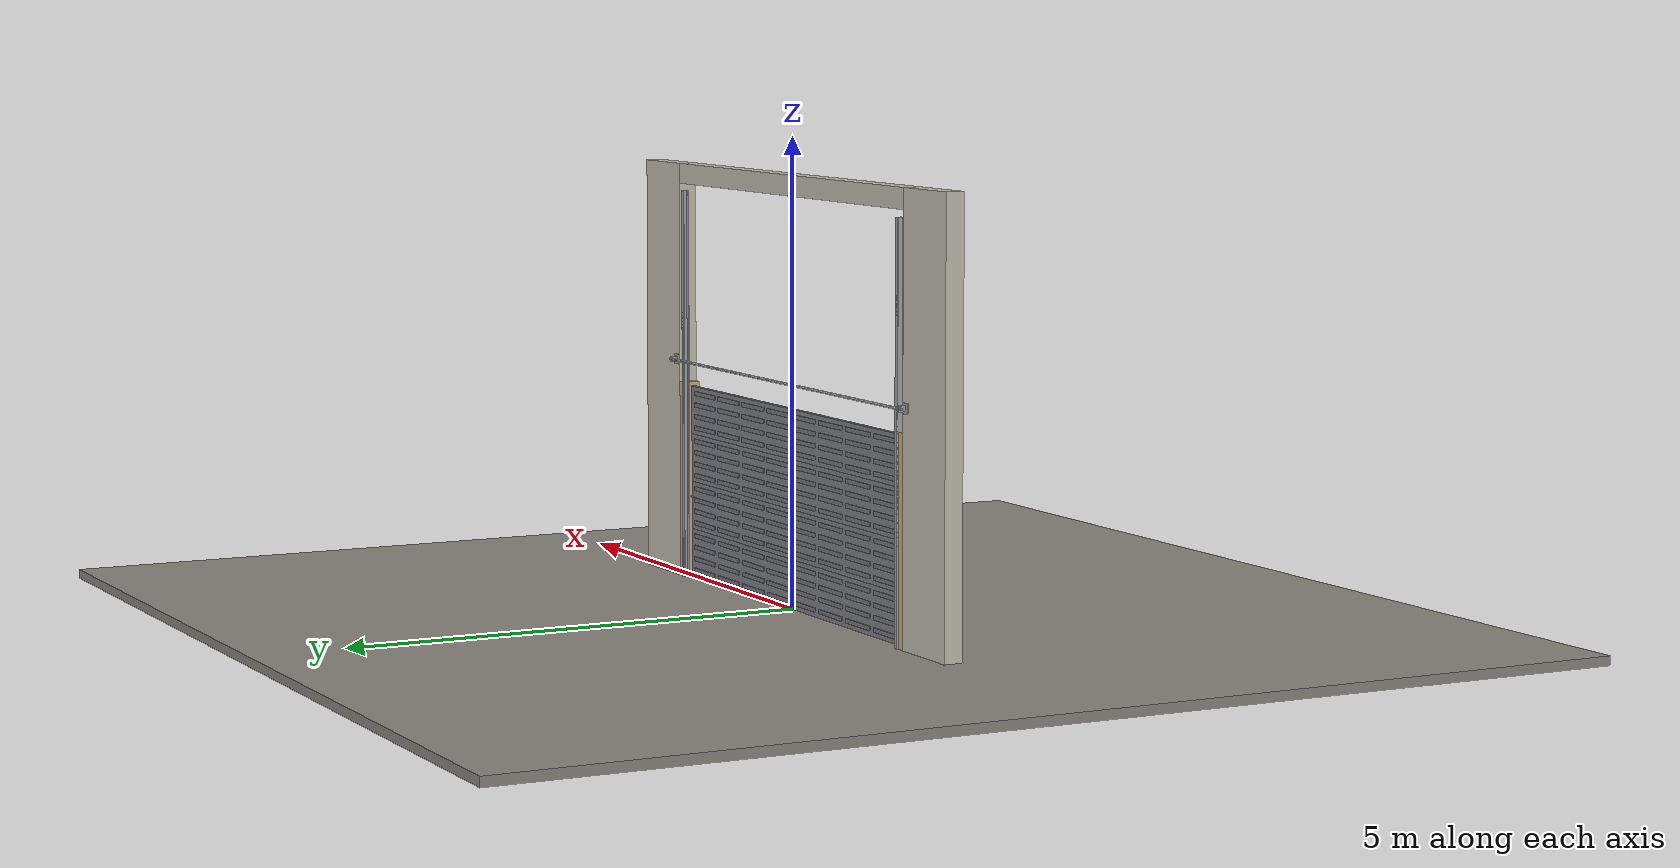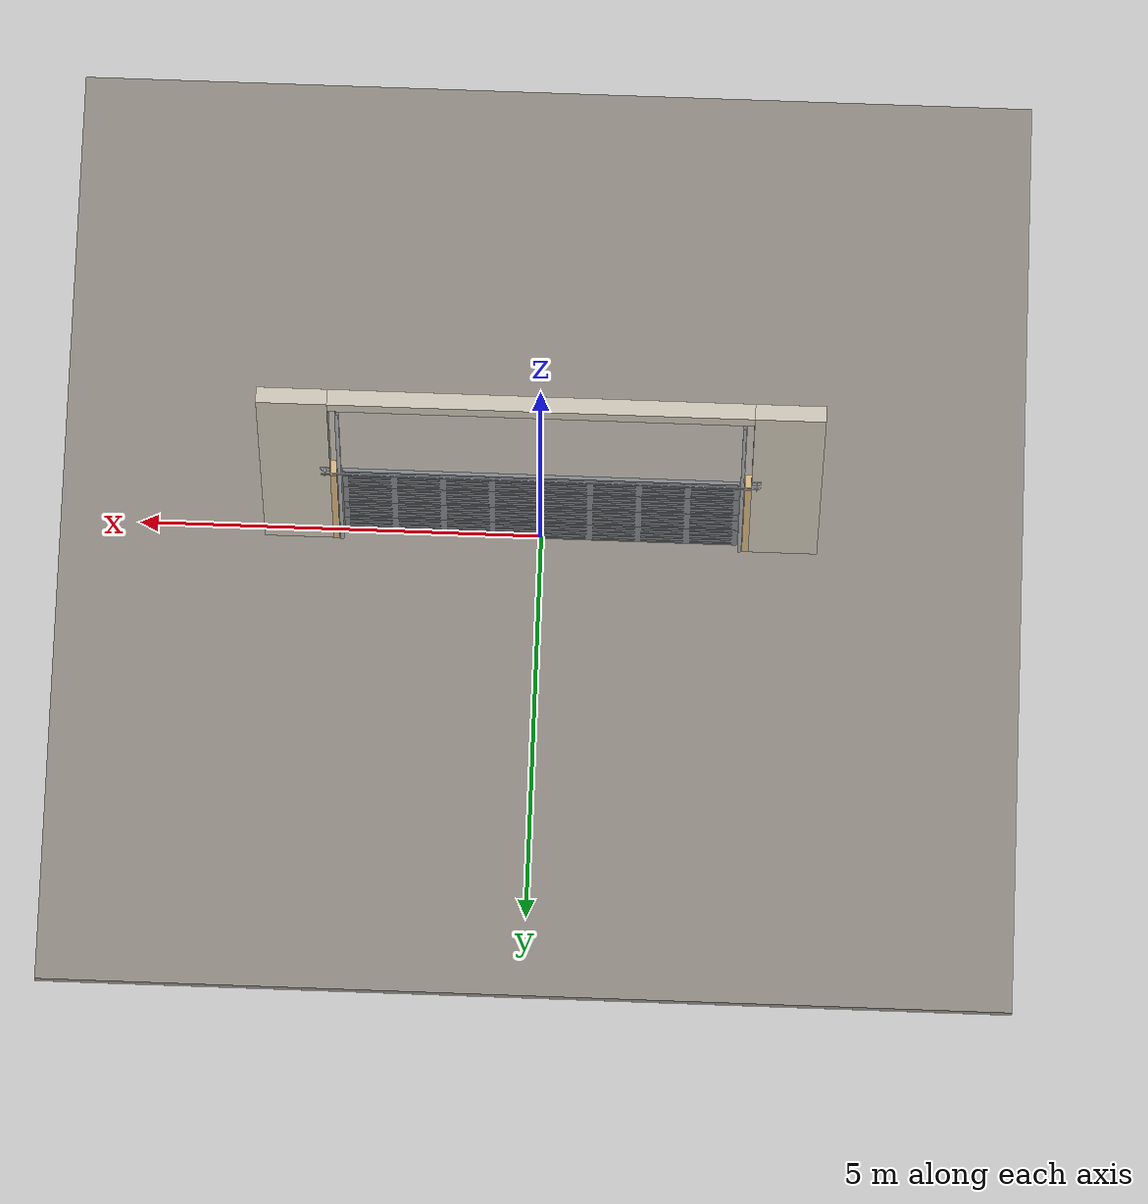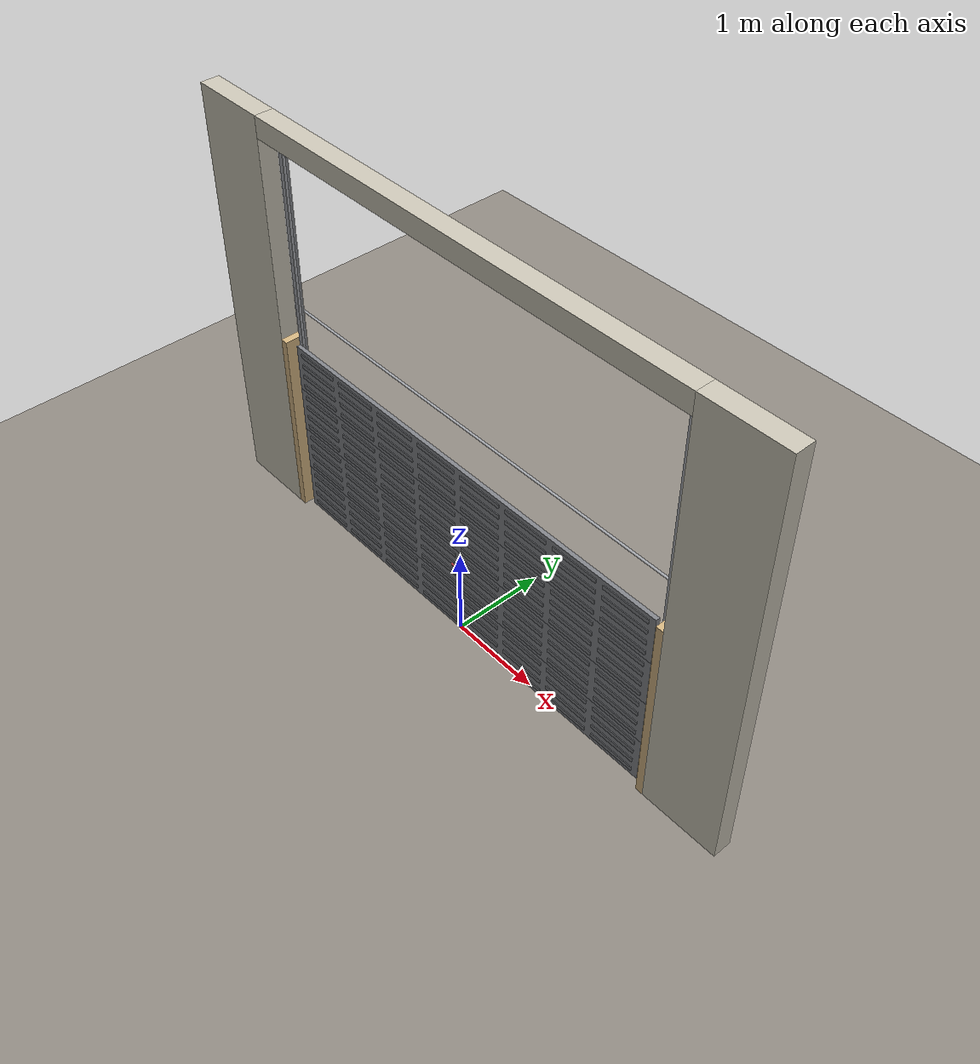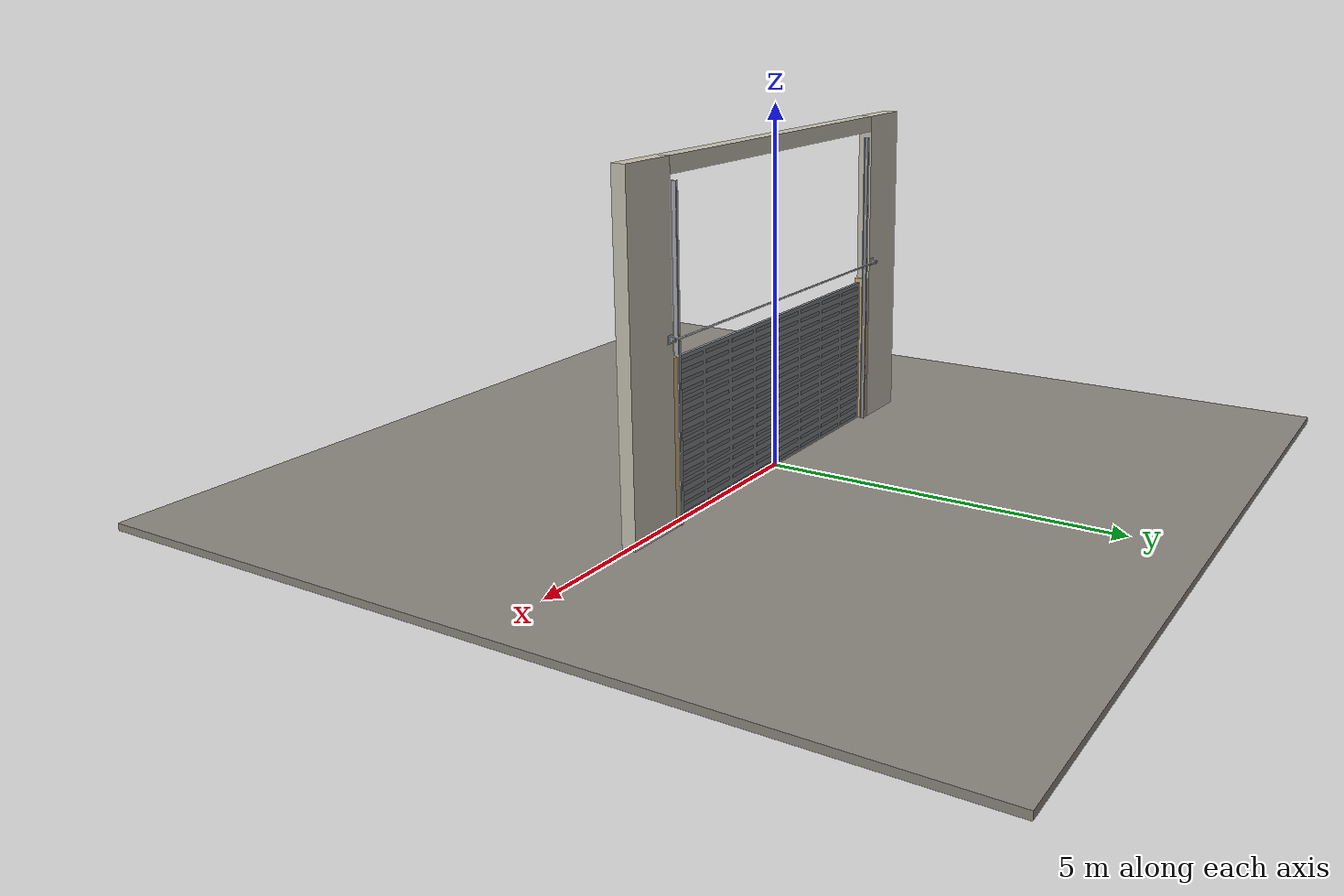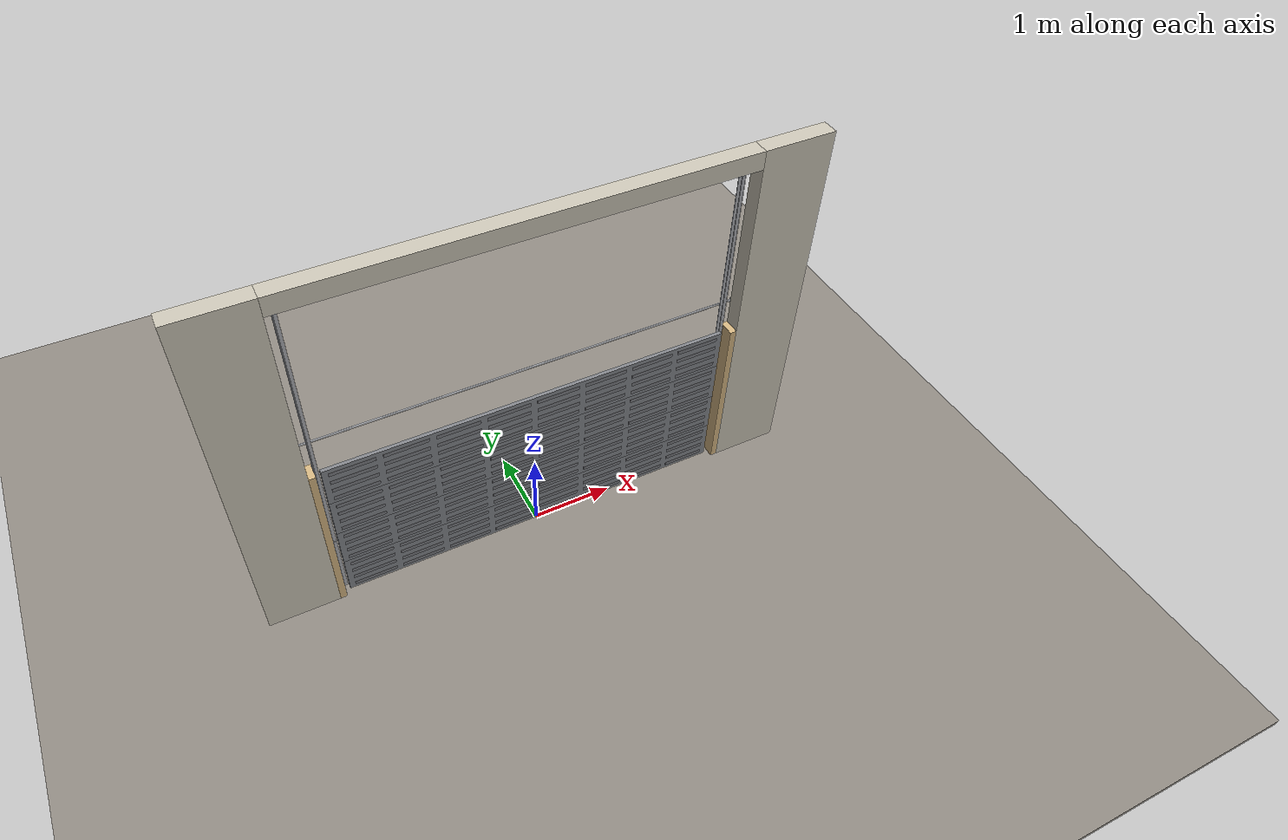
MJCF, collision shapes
<?xml version="1.0" ?>
<mujoco model="db0289_garage_sectional_simple">
  <compiler angle="radian" meshdir="../../hardware" texturedir="../../textures" autolimits="true" inertiafromgeom="false"/>
  <option timestep="0.002" integrator="implicitfast" cone="elliptic" impratio="10" noslip_iterations="3">
    <flag multiccd="enable"/>
  </option>
  <size memory="16M"/>
  <default>
    <geom condim="4" solref="0.005 1" solimp="0.95 0.99 0.001"/>
    <joint solreflimit="0.005 1" solimplimit="0.95 0.99 0.001"/>
    <tendon solreflimit="0.005 1"/>
    <equality solref="0.002 1"/>
  </default>
  <visual>
    <headlight ambient="0.4 0.4 0.4" diffuse="0.7 0.7 0.7" specular="0.2 0.2 0.2"/>
    <quality shadowsize="4096"/>
    <map znear="0.01" zfar="60"/>
  </visual>
  <asset>
    <mesh name="lever_01c630149d" file="lever_01c630149d.obj"/>
    <material name="mat_floor" rgba="0.55 0.53 0.5 1" specular="0.2" shininess="0.15" reflectance="0"/>
    <material name="mat_wall" rgba="0.78 0.76 0.7 1" specular="0.2" shininess="0.1" reflectance="0"/>
    <material name="mat_frame" rgba="0.82 0.7 0.5 1" specular="0.2" shininess="0.45" reflectance="0"/>
    <material name="mat_track" rgba="0.65 0.66 0.68 1" specular="0.74" shininess="0.5" reflectance="0.36"/>
    <material name="mat_section_0" rgba="0.5 0.51 0.53 1" specular="0.23" shininess="0.3" reflectance="0.02"/>
    <material name="mat_section_0_panel" rgba="0.46 0.469 0.488 1" specular="0.23" shininess="0.3" reflectance="0.02"/>
    <material name="mat_section_1" rgba="0.5 0.51 0.53 1" specular="0.23" shininess="0.3" reflectance="0.02"/>
    <material name="mat_section_1_panel" rgba="0.46 0.469 0.488 1" specular="0.23" shininess="0.3" reflectance="0.02"/>
    <material name="mat_hinge_line" rgba="0.2 0.2 0.2 1" specular="0.2" shininess="0.3" reflectance="0"/>
    <material name="mat_section_2" rgba="0.5 0.51 0.53 1" specular="0.23" shininess="0.3" reflectance="0.02"/>
    <material name="mat_section_2_panel" rgba="0.46 0.469 0.488 1" specular="0.23" shininess="0.3" reflectance="0.02"/>
    <material name="mat_section_3" rgba="0.5 0.51 0.53 1" specular="0.23" shininess="0.3" reflectance="0.02"/>
    <material name="mat_section_3_panel" rgba="0.46 0.469 0.488 1" specular="0.23" shininess="0.3" reflectance="0.02"/>
    <material name="mat_spring" rgba="0.55 0.56 0.58 1" specular="0.8" shininess="0.55" reflectance="0.4"/>
    <material name="mat_opener" rgba="0.05 0.05 0.05 1" specular="0.38" shininess="0.3" reflectance="0.12"/>
    <material name="mat_op_black_matte_metal" rgba="0.05 0.05 0.05 1" specular="0.38" shininess="0.3" reflectance="0.12"/>
    <material name="mat_trim" rgba="0.85 0.66 0.3 1" specular="0.8" shininess="0.75" reflectance="0.4"/>
    <material name="mat_lockbar" rgba="0.65 0.66 0.68 1" specular="0.74" shininess="0.5" reflectance="0.36"/>
    <texture name="skybox" type="skybox" builtin="gradient" rgb1="0.6 0.7 0.85" rgb2="0.9 0.92 0.95" width="256" height="256"/>
  </asset>
  <worldbody>
    <light name="sun" pos="1.5 -2.5 4" dir="-0.3 0.5 -0.8" directional="true" diffuse="0.8 0.8 0.8" specular="0.3 0.3 0.3" castshadow="true"/>
    <light name="fill" pos="-1.5 2.5 3" dir="0.3 -0.5 -0.7" directional="true" diffuse="0.35 0.35 0.4" castshadow="false"/>
    <camera name="robot_view" pos="0 -5.246875 2.559125" xyaxes="1 0 0 0 0.26963 0.962964" fovy="52"/>
    <camera name="far_view" pos="0 5.246875 2.559125" xyaxes="-1 0 0 0 -0.26963 0.962964" fovy="52"/>
    <camera name="iso" pos="3.987625 -4.407375 3.398625" xyaxes="0.741536 0.670913 0 -0.242917 0.268487 0.932151" fovy="46"/>
    <camera name="detail_handle" pos="0.2115 -1.1625 1.25" xyaxes="0.975133 0.221621 0 -0.065674 0.288965 0.955084" fovy="38"/>
    <geom name="floor" type="box" size="6 6 0.05" pos="0 0 -0.05" material="mat_floor" group="0" contype="1" conaffinity="1" friction="0.8 0.005 0.0001" density="2400"/>
    <geom name="wall_left" type="box" size="0.4275 0.1 2.305" pos="-3.0125 0 2.305" material="mat_wall" group="0" contype="1" conaffinity="1" friction="0.6 0.005 0.0001" density="800"/>
    <geom name="wall_right" type="box" size="0.4275 0.1 2.305" pos="3.0125 0 2.305" material="mat_wall" group="0" contype="1" conaffinity="1" friction="0.6 0.005 0.0001" density="800"/>
    <geom name="wall_header" type="box" size="2.585 0.1 0.11" pos="0 0 4.5" material="mat_wall" group="0" contype="1" conaffinity="1" friction="0.6 0.005 0.0001" density="800"/>
    <geom name="garage_jamb_l" type="box" size="0.04 0.1 1.09" pos="-2.545 0 1.09" material="mat_frame" group="0" contype="1" conaffinity="1" friction="0.6 0.005 0.0001" density="400"/>
    <geom name="garage_jamb_r" type="box" size="0.04 0.1 1.09" pos="2.545 0 1.09" material="mat_frame" group="0" contype="1" conaffinity="1" friction="0.6 0.005 0.0001" density="400"/>
    <geom name="track_l" type="box" size="0.004 0.033 2.155" pos="-2.49 0.0825 2.155" material="mat_track" group="0" contype="1" conaffinity="1" friction="0.6 0.005 0.0001" density="7850"/>
    <geom name="track_l_flange_n" type="box" size="0.022 0.004 2.155" pos="-2.472 0.0535 2.155" material="mat_track" group="0" contype="1" conaffinity="1" friction="0.6 0.005 0.0001" density="7850"/>
    <geom name="track_l_flange_p" type="box" size="0.022 0.004 2.155" pos="-2.472 0.1115 2.155" material="mat_track" group="0" contype="1" conaffinity="1" friction="0.6 0.005 0.0001" density="7850"/>
    <geom name="track_r" type="box" size="0.004 0.033 2.155" pos="2.49 0.0825 2.155" material="mat_track" group="0" contype="1" conaffinity="1" friction="0.6 0.005 0.0001" density="7850"/>
    <geom name="track_r_flange_n" type="box" size="0.022 0.004 2.155" pos="2.472 0.0535 2.155" material="mat_track" group="0" contype="1" conaffinity="1" friction="0.6 0.005 0.0001" density="7850"/>
    <geom name="track_r_flange_p" type="box" size="0.022 0.004 2.155" pos="2.472 0.1115 2.155" material="mat_track" group="0" contype="1" conaffinity="1" friction="0.6 0.005 0.0001" density="7850"/>
    <geom name="torsion_shaft" type="cylinder" size="0.013 2.695" pos="0 0.17 2.43" quat="0.707107 0 0.707107 0" material="mat_track" group="0" contype="1" conaffinity="1" friction="0.6 0.005 0.0001" density="7850"/>
    <geom name="torsion_bearing_plate_l" type="box" size="0.055 0.004 0.055" pos="-2.645 0.104 2.43" material="mat_track" group="1" contype="0" conaffinity="0" density="7850"/>
    <geom name="torsion_bearing_arm_l" type="box" size="0.008 0.049 0.03" pos="-2.645 0.139 2.43" material="mat_track" group="1" contype="0" conaffinity="0" density="7850"/>
    <geom name="torsion_bearing_plate_r" type="box" size="0.055 0.004 0.055" pos="2.645 0.104 2.43" material="mat_track" group="1" contype="0" conaffinity="0" density="7850"/>
    <geom name="torsion_bearing_arm_r" type="box" size="0.008 0.049 0.03" pos="2.645 0.139 2.43" material="mat_track" group="1" contype="0" conaffinity="0" density="7850"/>
    <site name="approach_point" pos="0 -2 0" quat="1 0 0 0" size="0.05" rgba="0.2 0.9 0.2 0.5" group="4"/>
    <site name="goal_point" pos="0 2 0" quat="1 0 0 0" size="0.05" rgba="0.2 0.9 0.2 0.5" group="4"/>
    <site name="door_plane_center" pos="0 0 1.09" quat="1 0 0 0" size="0.02" rgba="0.2 0.9 0.2 0.5" group="4"/>
    <body name="door" pos="0 0 0">
      <inertial pos="0 0 1.075" mass="113.015954" quat="0.707107 0.707107 0 0" diaginertia="42.747484032 224.300850795 267.010154451"/>
      <joint name="door_slide" type="slide" axis="0 0 1" limited="true" range="0 0.003" damping="7.676462" frictionloss="22.26683" stiffness="152.60131" springref="6.933333" armature="0.5"/>
      <geom name="section_0_slab" type="box" size="2.44 0.0225 0.26625" pos="0 0 0.27625" material="mat_section_0" group="0" contype="1" conaffinity="1" friction="0.4 0.005 0.0001" density="1"/>
      <geom name="section_0_panel_0_n" type="box" size="0.26125 0.003 0.024062" pos="-2.10875 -0.0255 0.084062" material="mat_section_0_panel" group="1" contype="0" conaffinity="0" density="1"/>
      <geom name="section_0_panel_0_p" type="box" size="0.26125 0.003 0.024062" pos="-2.10875 0.0255 0.084062" material="mat_section_0_panel" group="1" contype="0" conaffinity="0" density="1"/>
      <geom name="section_0_panel_1_n" type="box" size="0.26125 0.003 0.024062" pos="-1.50625 -0.0255 0.084062" material="mat_section_0_panel" group="1" contype="0" conaffinity="0" density="1"/>
      <geom name="section_0_panel_1_p" type="box" size="0.26125 0.003 0.024062" pos="-1.50625 0.0255 0.084062" material="mat_section_0_panel" group="1" contype="0" conaffinity="0" density="1"/>
      <geom name="section_0_panel_2_n" type="box" size="0.26125 0.003 0.024062" pos="-0.90375 -0.0255 0.084062" material="mat_section_0_panel" group="1" contype="0" conaffinity="0" density="1"/>
      <geom name="section_0_panel_2_p" type="box" size="0.26125 0.003 0.024062" pos="-0.90375 0.0255 0.084062" material="mat_section_0_panel" group="1" contype="0" conaffinity="0" density="1"/>
      <geom name="section_0_panel_3_n" type="box" size="0.26125 0.003 0.024062" pos="-0.30125 -0.0255 0.084062" material="mat_section_0_panel" group="1" contype="0" conaffinity="0" density="1"/>
      <geom name="section_0_panel_3_p" type="box" size="0.26125 0.003 0.024062" pos="-0.30125 0.0255 0.084062" material="mat_section_0_panel" group="1" contype="0" conaffinity="0" density="1"/>
      <geom name="section_0_panel_4_n" type="box" size="0.26125 0.003 0.024062" pos="0.30125 -0.0255 0.084062" material="mat_section_0_panel" group="1" contype="0" conaffinity="0" density="1"/>
      <geom name="section_0_panel_4_p" type="box" size="0.26125 0.003 0.024062" pos="0.30125 0.0255 0.084062" material="mat_section_0_panel" group="1" contype="0" conaffinity="0" density="1"/>
      <geom name="section_0_panel_5_n" type="box" size="0.26125 0.003 0.024062" pos="0.90375 -0.0255 0.084062" material="mat_section_0_panel" group="1" contype="0" conaffinity="0" density="1"/>
      <geom name="section_0_panel_5_p" type="box" size="0.26125 0.003 0.024062" pos="0.90375 0.0255 0.084062" material="mat_section_0_panel" group="1" contype="0" conaffinity="0" density="1"/>
      <geom name="section_0_panel_6_n" type="box" size="0.26125 0.003 0.024062" pos="1.50625 -0.0255 0.084062" material="mat_section_0_panel" group="1" contype="0" conaffinity="0" density="1"/>
      <geom name="section_0_panel_6_p" type="box" size="0.26125 0.003 0.024062" pos="1.50625 0.0255 0.084062" material="mat_section_0_panel" group="1" contype="0" conaffinity="0" density="1"/>
      <geom name="section_0_panel_7_n" type="box" size="0.26125 0.003 0.024062" pos="2.10875 -0.0255 0.084062" material="mat_section_0_panel" group="1" contype="0" conaffinity="0" density="1"/>
      <geom name="section_0_panel_7_p" type="box" size="0.26125 0.003 0.024062" pos="2.10875 0.0255 0.084062" material="mat_section_0_panel" group="1" contype="0" conaffinity="0" density="1"/>
      <geom name="section_0_panel_8_n" type="box" size="0.26125 0.003 0.024062" pos="-2.10875 -0.0255 0.212188" material="mat_section_0_panel" group="1" contype="0" conaffinity="0" density="1"/>
      <geom name="section_0_panel_8_p" type="box" size="0.26125 0.003 0.024062" pos="-2.10875 0.0255 0.212188" material="mat_section_0_panel" group="1" contype="0" conaffinity="0" density="1"/>
      <geom name="section_0_panel_9_n" type="box" size="0.26125 0.003 0.024062" pos="-1.50625 -0.0255 0.212188" material="mat_section_0_panel" group="1" contype="0" conaffinity="0" density="1"/>
      <geom name="section_0_panel_9_p" type="box" size="0.26125 0.003 0.024062" pos="-1.50625 0.0255 0.212188" material="mat_section_0_panel" group="1" contype="0" conaffinity="0" density="1"/>
      <geom name="section_0_panel_10_n" type="box" size="0.26125 0.003 0.024062" pos="-0.90375 -0.0255 0.212188" material="mat_section_0_panel" group="1" contype="0" conaffinity="0" density="1"/>
      <geom name="section_0_panel_10_p" type="box" size="0.26125 0.003 0.024062" pos="-0.90375 0.0255 0.212188" material="mat_section_0_panel" group="1" contype="0" conaffinity="0" density="1"/>
      <geom name="section_0_panel_11_n" type="box" size="0.26125 0.003 0.024062" pos="-0.30125 -0.0255 0.212188" material="mat_section_0_panel" group="1" contype="0" conaffinity="0" density="1"/>
      <geom name="section_0_panel_11_p" type="box" size="0.26125 0.003 0.024062" pos="-0.30125 0.0255 0.212188" material="mat_section_0_panel" group="1" contype="0" conaffinity="0" density="1"/>
      <geom name="section_0_panel_12_n" type="box" size="0.26125 0.003 0.024062" pos="0.30125 -0.0255 0.212188" material="mat_section_0_panel" group="1" contype="0" conaffinity="0" density="1"/>
      <geom name="section_0_panel_12_p" type="box" size="0.26125 0.003 0.024062" pos="0.30125 0.0255 0.212188" material="mat_section_0_panel" group="1" contype="0" conaffinity="0" density="1"/>
      <geom name="section_0_panel_13_n" type="box" size="0.26125 0.003 0.024062" pos="0.90375 -0.0255 0.212188" material="mat_section_0_panel" group="1" contype="0" conaffinity="0" density="1"/>
      <geom name="section_0_panel_13_p" type="box" size="0.26125 0.003 0.024062" pos="0.90375 0.0255 0.212188" material="mat_section_0_panel" group="1" contype="0" conaffinity="0" density="1"/>
      <geom name="section_0_panel_14_n" type="box" size="0.26125 0.003 0.024062" pos="1.50625 -0.0255 0.212188" material="mat_section_0_panel" group="1" contype="0" conaffinity="0" density="1"/>
      <geom name="section_0_panel_14_p" type="box" size="0.26125 0.003 0.024062" pos="1.50625 0.0255 0.212188" material="mat_section_0_panel" group="1" contype="0" conaffinity="0" density="1"/>
      <geom name="section_0_panel_15_n" type="box" size="0.26125 0.003 0.024062" pos="2.10875 -0.0255 0.212188" material="mat_section_0_panel" group="1" contype="0" conaffinity="0" density="1"/>
      <geom name="section_0_panel_15_p" type="box" size="0.26125 0.003 0.024062" pos="2.10875 0.0255 0.212188" material="mat_section_0_panel" group="1" contype="0" conaffinity="0" density="1"/>
      <geom name="section_0_panel_16_n" type="box" size="0.26125 0.003 0.024062" pos="-2.10875 -0.0255 0.340313" material="mat_section_0_panel" group="1" contype="0" conaffinity="0" density="1"/>
      <geom name="section_0_panel_16_p" type="box" size="0.26125 0.003 0.024062" pos="-2.10875 0.0255 0.340313" material="mat_section_0_panel" group="1" contype="0" conaffinity="0" density="1"/>
      <geom name="section_0_panel_17_n" type="box" size="0.26125 0.003 0.024062" pos="-1.50625 -0.0255 0.340313" material="mat_section_0_panel" group="1" contype="0" conaffinity="0" density="1"/>
      <geom name="section_0_panel_17_p" type="box" size="0.26125 0.003 0.024062" pos="-1.50625 0.0255 0.340313" material="mat_section_0_panel" group="1" contype="0" conaffinity="0" density="1"/>
      <geom name="section_0_panel_18_n" type="box" size="0.26125 0.003 0.024062" pos="-0.90375 -0.0255 0.340313" material="mat_section_0_panel" group="1" contype="0" conaffinity="0" density="1"/>
      <geom name="section_0_panel_18_p" type="box" size="0.26125 0.003 0.024062" pos="-0.90375 0.0255 0.340313" material="mat_section_0_panel" group="1" contype="0" conaffinity="0" density="1"/>
      <geom name="section_0_panel_19_n" type="box" size="0.26125 0.003 0.024062" pos="-0.30125 -0.0255 0.340313" material="mat_section_0_panel" group="1" contype="0" conaffinity="0" density="1"/>
      <geom name="section_0_panel_19_p" type="box" size="0.26125 0.003 0.024062" pos="-0.30125 0.0255 0.340313" material="mat_section_0_panel" group="1" contype="0" conaffinity="0" density="1"/>
      <geom name="section_0_panel_20_n" type="box" size="0.26125 0.003 0.024062" pos="0.30125 -0.0255 0.340313" material="mat_section_0_panel" group="1" contype="0" conaffinity="0" density="1"/>
      <geom name="section_0_panel_20_p" type="box" size="0.26125 0.003 0.024062" pos="0.30125 0.0255 0.340313" material="mat_section_0_panel" group="1" contype="0" conaffinity="0" density="1"/>
      <geom name="section_0_panel_21_n" type="box" size="0.26125 0.003 0.024062" pos="0.90375 -0.0255 0.340313" material="mat_section_0_panel" group="1" contype="0" conaffinity="0" density="1"/>
      <geom name="section_0_panel_21_p" type="box" size="0.26125 0.003 0.024062" pos="0.90375 0.0255 0.340313" material="mat_section_0_panel" group="1" contype="0" conaffinity="0" density="1"/>
      <geom name="section_0_panel_22_n" type="box" size="0.26125 0.003 0.024062" pos="1.50625 -0.0255 0.340313" material="mat_section_0_panel" group="1" contype="0" conaffinity="0" density="1"/>
      <geom name="section_0_panel_22_p" type="box" size="0.26125 0.003 0.024062" pos="1.50625 0.0255 0.340313" material="mat_section_0_panel" group="1" contype="0" conaffinity="0" density="1"/>
      <geom name="section_0_panel_23_n" type="box" size="0.26125 0.003 0.024062" pos="2.10875 -0.0255 0.340313" material="mat_section_0_panel" group="1" contype="0" conaffinity="0" density="1"/>
      <geom name="section_0_panel_23_p" type="box" size="0.26125 0.003 0.024062" pos="2.10875 0.0255 0.340313" material="mat_section_0_panel" group="1" contype="0" conaffinity="0" density="1"/>
      <geom name="section_0_panel_24_n" type="box" size="0.26125 0.003 0.024062" pos="-2.10875 -0.0255 0.468437" material="mat_section_0_panel" group="1" contype="0" conaffinity="0" density="1"/>
      <geom name="section_0_panel_24_p" type="box" size="0.26125 0.003 0.024062" pos="-2.10875 0.0255 0.468437" material="mat_section_0_panel" group="1" contype="0" conaffinity="0" density="1"/>
      <geom name="section_0_panel_25_n" type="box" size="0.26125 0.003 0.024062" pos="-1.50625 -0.0255 0.468437" material="mat_section_0_panel" group="1" contype="0" conaffinity="0" density="1"/>
      <geom name="section_0_panel_25_p" type="box" size="0.26125 0.003 0.024062" pos="-1.50625 0.0255 0.468437" material="mat_section_0_panel" group="1" contype="0" conaffinity="0" density="1"/>
      <geom name="section_0_panel_26_n" type="box" size="0.26125 0.003 0.024062" pos="-0.90375 -0.0255 0.468437" material="mat_section_0_panel" group="1" contype="0" conaffinity="0" density="1"/>
      <geom name="section_0_panel_26_p" type="box" size="0.26125 0.003 0.024062" pos="-0.90375 0.0255 0.468437" material="mat_section_0_panel" group="1" contype="0" conaffinity="0" density="1"/>
      <geom name="section_0_panel_27_n" type="box" size="0.26125 0.003 0.024062" pos="-0.30125 -0.0255 0.468437" material="mat_section_0_panel" group="1" contype="0" conaffinity="0" density="1"/>
      <geom name="section_0_panel_27_p" type="box" size="0.26125 0.003 0.024062" pos="-0.30125 0.0255 0.468437" material="mat_section_0_panel" group="1" contype="0" conaffinity="0" density="1"/>
      <geom name="section_0_panel_28_n" type="box" size="0.26125 0.003 0.024062" pos="0.30125 -0.0255 0.468437" material="mat_section_0_panel" group="1" contype="0" conaffinity="0" density="1"/>
      <geom name="section_0_panel_28_p" type="box" size="0.26125 0.003 0.024062" pos="0.30125 0.0255 0.468437" material="mat_section_0_panel" group="1" contype="0" conaffinity="0" density="1"/>
      <geom name="section_0_panel_29_n" type="box" size="0.26125 0.003 0.024062" pos="0.90375 -0.0255 0.468437" material="mat_section_0_panel" group="1" contype="0" conaffinity="0" density="1"/>
      <geom name="section_0_panel_29_p" type="box" size="0.26125 0.003 0.024062" pos="0.90375 0.0255 0.468437" material="mat_section_0_panel" group="1" contype="0" conaffinity="0" density="1"/>
      <geom name="section_0_panel_30_n" type="box" size="0.26125 0.003 0.024062" pos="1.50625 -0.0255 0.468437" material="mat_section_0_panel" group="1" contype="0" conaffinity="0" density="1"/>
      <geom name="section_0_panel_30_p" type="box" size="0.26125 0.003 0.024062" pos="1.50625 0.0255 0.468437" material="mat_section_0_panel" group="1" contype="0" conaffinity="0" density="1"/>
      <geom name="section_0_panel_31_n" type="box" size="0.26125 0.003 0.024062" pos="2.10875 -0.0255 0.468437" material="mat_section_0_panel" group="1" contype="0" conaffinity="0" density="1"/>
      <geom name="section_0_panel_31_p" type="box" size="0.26125 0.003 0.024062" pos="2.10875 0.0255 0.468437" material="mat_section_0_panel" group="1" contype="0" conaffinity="0" density="1"/>
      <geom name="section_1_slab" type="box" size="2.44 0.0225 0.26625" pos="0 0 0.80875" material="mat_section_1" group="0" contype="1" conaffinity="1" friction="0.4 0.005 0.0001" density="1"/>
      <geom name="section_1_panel_0_n" type="box" size="0.26125 0.003 0.024062" pos="-2.10875 -0.0255 0.616563" material="mat_section_1_panel" group="1" contype="0" conaffinity="0" density="1"/>
      <geom name="section_1_panel_0_p" type="box" size="0.26125 0.003 0.024062" pos="-2.10875 0.0255 0.616563" material="mat_section_1_panel" group="1" contype="0" conaffinity="0" density="1"/>
      <geom name="section_1_panel_1_n" type="box" size="0.26125 0.003 0.024062" pos="-1.50625 -0.0255 0.616563" material="mat_section_1_panel" group="1" contype="0" conaffinity="0" density="1"/>
      <geom name="section_1_panel_1_p" type="box" size="0.26125 0.003 0.024062" pos="-1.50625 0.0255 0.616563" material="mat_section_1_panel" group="1" contype="0" conaffinity="0" density="1"/>
      <geom name="section_1_panel_2_n" type="box" size="0.26125 0.003 0.024062" pos="-0.90375 -0.0255 0.616563" material="mat_section_1_panel" group="1" contype="0" conaffinity="0" density="1"/>
      <geom name="section_1_panel_2_p" type="box" size="0.26125 0.003 0.024062" pos="-0.90375 0.0255 0.616563" material="mat_section_1_panel" group="1" contype="0" conaffinity="0" density="1"/>
      <geom name="section_1_panel_3_n" type="box" size="0.26125 0.003 0.024062" pos="-0.30125 -0.0255 0.616563" material="mat_section_1_panel" group="1" contype="0" conaffinity="0" density="1"/>
      <geom name="section_1_panel_3_p" type="box" size="0.26125 0.003 0.024062" pos="-0.30125 0.0255 0.616563" material="mat_section_1_panel" group="1" contype="0" conaffinity="0" density="1"/>
      <geom name="section_1_panel_4_n" type="box" size="0.26125 0.003 0.024062" pos="0.30125 -0.0255 0.616563" material="mat_section_1_panel" group="1" contype="0" conaffinity="0" density="1"/>
      <geom name="section_1_panel_4_p" type="box" size="0.26125 0.003 0.024062" pos="0.30125 0.0255 0.616563" material="mat_section_1_panel" group="1" contype="0" conaffinity="0" density="1"/>
      <geom name="section_1_panel_5_n" type="box" size="0.26125 0.003 0.024062" pos="0.90375 -0.0255 0.616563" material="mat_section_1_panel" group="1" contype="0" conaffinity="0" density="1"/>
      <geom name="section_1_panel_5_p" type="box" size="0.26125 0.003 0.024062" pos="0.90375 0.0255 0.616563" material="mat_section_1_panel" group="1" contype="0" conaffinity="0" density="1"/>
      <geom name="section_1_panel_6_n" type="box" size="0.26125 0.003 0.024062" pos="1.50625 -0.0255 0.616563" material="mat_section_1_panel" group="1" contype="0" conaffinity="0" density="1"/>
      <geom name="section_1_panel_6_p" type="box" size="0.26125 0.003 0.024062" pos="1.50625 0.0255 0.616563" material="mat_section_1_panel" group="1" contype="0" conaffinity="0" density="1"/>
      <geom name="section_1_panel_7_n" type="box" size="0.26125 0.003 0.024062" pos="2.10875 -0.0255 0.616563" material="mat_section_1_panel" group="1" contype="0" conaffinity="0" density="1"/>
      <geom name="section_1_panel_7_p" type="box" size="0.26125 0.003 0.024062" pos="2.10875 0.0255 0.616563" material="mat_section_1_panel" group="1" contype="0" conaffinity="0" density="1"/>
      <geom name="section_1_panel_8_n" type="box" size="0.26125 0.003 0.024062" pos="-2.10875 -0.0255 0.744687" material="mat_section_1_panel" group="1" contype="0" conaffinity="0" density="1"/>
      <geom name="section_1_panel_8_p" type="box" size="0.26125 0.003 0.024062" pos="-2.10875 0.0255 0.744687" material="mat_section_1_panel" group="1" contype="0" conaffinity="0" density="1"/>
      <geom name="section_1_panel_9_n" type="box" size="0.26125 0.003 0.024062" pos="-1.50625 -0.0255 0.744687" material="mat_section_1_panel" group="1" contype="0" conaffinity="0" density="1"/>
      <geom name="section_1_panel_9_p" type="box" size="0.26125 0.003 0.024062" pos="-1.50625 0.0255 0.744687" material="mat_section_1_panel" group="1" contype="0" conaffinity="0" density="1"/>
      <geom name="section_1_panel_10_n" type="box" size="0.26125 0.003 0.024062" pos="-0.90375 -0.0255 0.744687" material="mat_section_1_panel" group="1" contype="0" conaffinity="0" density="1"/>
      <geom name="section_1_panel_10_p" type="box" size="0.26125 0.003 0.024062" pos="-0.90375 0.0255 0.744687" material="mat_section_1_panel" group="1" contype="0" conaffinity="0" density="1"/>
      <geom name="section_1_panel_11_n" type="box" size="0.26125 0.003 0.024062" pos="-0.30125 -0.0255 0.744687" material="mat_section_1_panel" group="1" contype="0" conaffinity="0" density="1"/>
      <geom name="section_1_panel_11_p" type="box" size="0.26125 0.003 0.024062" pos="-0.30125 0.0255 0.744687" material="mat_section_1_panel" group="1" contype="0" conaffinity="0" density="1"/>
      <geom name="section_1_panel_12_n" type="box" size="0.26125 0.003 0.024062" pos="0.30125 -0.0255 0.744687" material="mat_section_1_panel" group="1" contype="0" conaffinity="0" density="1"/>
      <geom name="section_1_panel_12_p" type="box" size="0.26125 0.003 0.024062" pos="0.30125 0.0255 0.744687" material="mat_section_1_panel" group="1" contype="0" conaffinity="0" density="1"/>
      <geom name="section_1_panel_13_n" type="box" size="0.26125 0.003 0.024062" pos="0.90375 -0.0255 0.744687" material="mat_section_1_panel" group="1" contype="0" conaffinity="0" density="1"/>
      <geom name="section_1_panel_13_p" type="box" size="0.26125 0.003 0.024062" pos="0.90375 0.0255 0.744687" material="mat_section_1_panel" group="1" contype="0" conaffinity="0" density="1"/>
      <geom name="section_1_panel_14_n" type="box" size="0.26125 0.003 0.024062" pos="1.50625 -0.0255 0.744687" material="mat_section_1_panel" group="1" contype="0" conaffinity="0" density="1"/>
      <geom name="section_1_panel_14_p" type="box" size="0.26125 0.003 0.024062" pos="1.50625 0.0255 0.744687" material="mat_section_1_panel" group="1" contype="0" conaffinity="0" density="1"/>
      <geom name="section_1_panel_15_n" type="box" size="0.26125 0.003 0.024062" pos="2.10875 -0.0255 0.744687" material="mat_section_1_panel" group="1" contype="0" conaffinity="0" density="1"/>
      <geom name="section_1_panel_15_p" type="box" size="0.26125 0.003 0.024062" pos="2.10875 0.0255 0.744687" material="mat_section_1_panel" group="1" contype="0" conaffinity="0" density="1"/>
      <geom name="section_1_panel_16_n" type="box" size="0.26125 0.003 0.024062" pos="-2.10875 -0.0255 0.872812" material="mat_section_1_panel" group="1" contype="0" conaffinity="0" density="1"/>
      <geom name="section_1_panel_16_p" type="box" size="0.26125 0.003 0.024062" pos="-2.10875 0.0255 0.872812" material="mat_section_1_panel" group="1" contype="0" conaffinity="0" density="1"/>
      <geom name="section_1_panel_17_n" type="box" size="0.26125 0.003 0.024062" pos="-1.50625 -0.0255 0.872812" material="mat_section_1_panel" group="1" contype="0" conaffinity="0" density="1"/>
      <geom name="section_1_panel_17_p" type="box" size="0.26125 0.003 0.024062" pos="-1.50625 0.0255 0.872812" material="mat_section_1_panel" group="1" contype="0" conaffinity="0" density="1"/>
      <geom name="section_1_panel_18_n" type="box" size="0.26125 0.003 0.024062" pos="-0.90375 -0.0255 0.872812" material="mat_section_1_panel" group="1" contype="0" conaffinity="0" density="1"/>
      <geom name="section_1_panel_18_p" type="box" size="0.26125 0.003 0.024062" pos="-0.90375 0.0255 0.872812" material="mat_section_1_panel" group="1" contype="0" conaffinity="0" density="1"/>
      <geom name="section_1_panel_19_n" type="box" size="0.26125 0.003 0.024062" pos="-0.30125 -0.0255 0.872812" material="mat_section_1_panel" group="1" contype="0" conaffinity="0" density="1"/>
      <geom name="section_1_panel_19_p" type="box" size="0.26125 0.003 0.024062" pos="-0.30125 0.0255 0.872812" material="mat_section_1_panel" group="1" contype="0" conaffinity="0" density="1"/>
      <geom name="section_1_panel_20_n" type="box" size="0.26125 0.003 0.024062" pos="0.30125 -0.0255 0.872812" material="mat_section_1_panel" group="1" contype="0" conaffinity="0" density="1"/>
      <geom name="section_1_panel_20_p" type="box" size="0.26125 0.003 0.024062" pos="0.30125 0.0255 0.872812" material="mat_section_1_panel" group="1" contype="0" conaffinity="0" density="1"/>
      <geom name="section_1_panel_21_n" type="box" size="0.26125 0.003 0.024062" pos="0.90375 -0.0255 0.872812" material="mat_section_1_panel" group="1" contype="0" conaffinity="0" density="1"/>
      <geom name="section_1_panel_21_p" type="box" size="0.26125 0.003 0.024062" pos="0.90375 0.0255 0.872812" material="mat_section_1_panel" group="1" contype="0" conaffinity="0" density="1"/>
      <geom name="section_1_panel_22_n" type="box" size="0.26125 0.003 0.024062" pos="1.50625 -0.0255 0.872812" material="mat_section_1_panel" group="1" contype="0" conaffinity="0" density="1"/>
      <geom name="section_1_panel_22_p" type="box" size="0.26125 0.003 0.024062" pos="1.50625 0.0255 0.872812" material="mat_section_1_panel" group="1" contype="0" conaffinity="0" density="1"/>
      <geom name="section_1_panel_23_n" type="box" size="0.26125 0.003 0.024062" pos="2.10875 -0.0255 0.872812" material="mat_section_1_panel" group="1" contype="0" conaffinity="0" density="1"/>
      <geom name="section_1_panel_23_p" type="box" size="0.26125 0.003 0.024062" pos="2.10875 0.0255 0.872812" material="mat_section_1_panel" group="1" contype="0" conaffinity="0" density="1"/>
      <geom name="section_1_panel_24_n" type="box" size="0.26125 0.003 0.024062" pos="-2.10875 -0.0255 1.000937" material="mat_section_1_panel" group="1" contype="0" conaffinity="0" density="1"/>
      <geom name="section_1_panel_24_p" type="box" size="0.26125 0.003 0.024062" pos="-2.10875 0.0255 1.000937" material="mat_section_1_panel" group="1" contype="0" conaffinity="0" density="1"/>
      <geom name="section_1_panel_25_n" type="box" size="0.26125 0.003 0.024062" pos="-1.50625 -0.0255 1.000937" material="mat_section_1_panel" group="1" contype="0" conaffinity="0" density="1"/>
      <geom name="section_1_panel_25_p" type="box" size="0.26125 0.003 0.024062" pos="-1.50625 0.0255 1.000937" material="mat_section_1_panel" group="1" contype="0" conaffinity="0" density="1"/>
      <geom name="section_1_panel_26_n" type="box" size="0.26125 0.003 0.024062" pos="-0.90375 -0.0255 1.000937" material="mat_section_1_panel" group="1" contype="0" conaffinity="0" density="1"/>
      <geom name="section_1_panel_26_p" type="box" size="0.26125 0.003 0.024062" pos="-0.90375 0.0255 1.000937" material="mat_section_1_panel" group="1" contype="0" conaffinity="0" density="1"/>
      <geom name="section_1_panel_27_n" type="box" size="0.26125 0.003 0.024062" pos="-0.30125 -0.0255 1.000937" material="mat_section_1_panel" group="1" contype="0" conaffinity="0" density="1"/>
      <geom name="section_1_panel_27_p" type="box" size="0.26125 0.003 0.024062" pos="-0.30125 0.0255 1.000937" material="mat_section_1_panel" group="1" contype="0" conaffinity="0" density="1"/>
      <geom name="section_1_panel_28_n" type="box" size="0.26125 0.003 0.024062" pos="0.30125 -0.0255 1.000937" material="mat_section_1_panel" group="1" contype="0" conaffinity="0" density="1"/>
      <geom name="section_1_panel_28_p" type="box" size="0.26125 0.003 0.024062" pos="0.30125 0.0255 1.000937" material="mat_section_1_panel" group="1" contype="0" conaffinity="0" density="1"/>
      <geom name="section_1_panel_29_n" type="box" size="0.26125 0.003 0.024062" pos="0.90375 -0.0255 1.000937" material="mat_section_1_panel" group="1" contype="0" conaffinity="0" density="1"/>
      <geom name="section_1_panel_29_p" type="box" size="0.26125 0.003 0.024062" pos="0.90375 0.0255 1.000937" material="mat_section_1_panel" group="1" contype="0" conaffinity="0" density="1"/>
      <geom name="section_1_panel_30_n" type="box" size="0.26125 0.003 0.024062" pos="1.50625 -0.0255 1.000937" material="mat_section_1_panel" group="1" contype="0" conaffinity="0" density="1"/>
      <geom name="section_1_panel_30_p" type="box" size="0.26125 0.003 0.024062" pos="1.50625 0.0255 1.000937" material="mat_section_1_panel" group="1" contype="0" conaffinity="0" density="1"/>
      <geom name="section_1_panel_31_n" type="box" size="0.26125 0.003 0.024062" pos="2.10875 -0.0255 1.000937" material="mat_section_1_panel" group="1" contype="0" conaffinity="0" density="1"/>
      <geom name="section_1_panel_31_p" type="box" size="0.26125 0.003 0.024062" pos="2.10875 0.0255 1.000937" material="mat_section_1_panel" group="1" contype="0" conaffinity="0" density="1"/>
      <geom name="section_2_slab" type="box" size="2.44 0.0225 0.26625" pos="0 0 1.34125" material="mat_section_2" group="0" contype="1" conaffinity="1" friction="0.4 0.005 0.0001" density="1"/>
      <geom name="section_2_panel_0_n" type="box" size="0.26125 0.003 0.024062" pos="-2.10875 -0.0255 1.149062" material="mat_section_2_panel" group="1" contype="0" conaffinity="0" density="1"/>
      <geom name="section_2_panel_0_p" type="box" size="0.26125 0.003 0.024062" pos="-2.10875 0.0255 1.149062" material="mat_section_2_panel" group="1" contype="0" conaffinity="0" density="1"/>
      <geom name="section_2_panel_1_n" type="box" size="0.26125 0.003 0.024062" pos="-1.50625 -0.0255 1.149062" material="mat_section_2_panel" group="1" contype="0" conaffinity="0" density="1"/>
      <geom name="section_2_panel_1_p" type="box" size="0.26125 0.003 0.024062" pos="-1.50625 0.0255 1.149062" material="mat_section_2_panel" group="1" contype="0" conaffinity="0" density="1"/>
      <geom name="section_2_panel_2_n" type="box" size="0.26125 0.003 0.024062" pos="-0.90375 -0.0255 1.149062" material="mat_section_2_panel" group="1" contype="0" conaffinity="0" density="1"/>
      <geom name="section_2_panel_2_p" type="box" size="0.26125 0.003 0.024062" pos="-0.90375 0.0255 1.149062" material="mat_section_2_panel" group="1" contype="0" conaffinity="0" density="1"/>
      <geom name="section_2_panel_3_n" type="box" size="0.26125 0.003 0.024062" pos="-0.30125 -0.0255 1.149062" material="mat_section_2_panel" group="1" contype="0" conaffinity="0" density="1"/>
      <geom name="section_2_panel_3_p" type="box" size="0.26125 0.003 0.024062" pos="-0.30125 0.0255 1.149062" material="mat_section_2_panel" group="1" contype="0" conaffinity="0" density="1"/>
      <geom name="section_2_panel_4_n" type="box" size="0.26125 0.003 0.024062" pos="0.30125 -0.0255 1.149062" material="mat_section_2_panel" group="1" contype="0" conaffinity="0" density="1"/>
      <geom name="section_2_panel_4_p" type="box" size="0.26125 0.003 0.024062" pos="0.30125 0.0255 1.149062" material="mat_section_2_panel" group="1" contype="0" conaffinity="0" density="1"/>
      <geom name="section_2_panel_5_n" type="box" size="0.26125 0.003 0.024062" pos="0.90375 -0.0255 1.149062" material="mat_section_2_panel" group="1" contype="0" conaffinity="0" density="1"/>
      <geom name="section_2_panel_5_p" type="box" size="0.26125 0.003 0.024062" pos="0.90375 0.0255 1.149062" material="mat_section_2_panel" group="1" contype="0" conaffinity="0" density="1"/>
      <geom name="section_2_panel_6_n" type="box" size="0.26125 0.003 0.024062" pos="1.50625 -0.0255 1.149062" material="mat_section_2_panel" group="1" contype="0" conaffinity="0" density="1"/>
      <geom name="section_2_panel_6_p" type="box" size="0.26125 0.003 0.024062" pos="1.50625 0.0255 1.149062" material="mat_section_2_panel" group="1" contype="0" conaffinity="0" density="1"/>
      <geom name="section_2_panel_7_n" type="box" size="0.26125 0.003 0.024062" pos="2.10875 -0.0255 1.149062" material="mat_section_2_panel" group="1" contype="0" conaffinity="0" density="1"/>
      <geom name="section_2_panel_7_p" type="box" size="0.26125 0.003 0.024062" pos="2.10875 0.0255 1.149062" material="mat_section_2_panel" group="1" contype="0" conaffinity="0" density="1"/>
      <geom name="section_2_panel_8_n" type="box" size="0.26125 0.003 0.024062" pos="-2.10875 -0.0255 1.277187" material="mat_section_2_panel" group="1" contype="0" conaffinity="0" density="1"/>
      <geom name="section_2_panel_8_p" type="box" size="0.26125 0.003 0.024062" pos="-2.10875 0.0255 1.277187" material="mat_section_2_panel" group="1" contype="0" conaffinity="0" density="1"/>
      <geom name="section_2_panel_9_n" type="box" size="0.26125 0.003 0.024062" pos="-1.50625 -0.0255 1.277187" material="mat_section_2_panel" group="1" contype="0" conaffinity="0" density="1"/>
      <geom name="section_2_panel_9_p" type="box" size="0.26125 0.003 0.024062" pos="-1.50625 0.0255 1.277187" material="mat_section_2_panel" group="1" contype="0" conaffinity="0" density="1"/>
      <geom name="section_2_panel_10_n" type="box" size="0.26125 0.003 0.024062" pos="-0.90375 -0.0255 1.277187" material="mat_section_2_panel" group="1" contype="0" conaffinity="0" density="1"/>
      <geom name="section_2_panel_10_p" type="box" size="0.26125 0.003 0.024062" pos="-0.90375 0.0255 1.277187" material="mat_section_2_panel" group="1" contype="0" conaffinity="0" density="1"/>
      <geom name="section_2_panel_11_n" type="box" size="0.26125 0.003 0.024062" pos="-0.30125 -0.0255 1.277187" material="mat_section_2_panel" group="1" contype="0" conaffinity="0" density="1"/>
      <geom name="section_2_panel_11_p" type="box" size="0.26125 0.003 0.024062" pos="-0.30125 0.0255 1.277187" material="mat_section_2_panel" group="1" contype="0" conaffinity="0" density="1"/>
      <geom name="section_2_panel_12_n" type="box" size="0.26125 0.003 0.024062" pos="0.30125 -0.0255 1.277187" material="mat_section_2_panel" group="1" contype="0" conaffinity="0" density="1"/>
      <geom name="section_2_panel_12_p" type="box" size="0.26125 0.003 0.024062" pos="0.30125 0.0255 1.277187" material="mat_section_2_panel" group="1" contype="0" conaffinity="0" density="1"/>
      <geom name="section_2_panel_13_n" type="box" size="0.26125 0.003 0.024062" pos="0.90375 -0.0255 1.277187" material="mat_section_2_panel" group="1" contype="0" conaffinity="0" density="1"/>
      <geom name="section_2_panel_13_p" type="box" size="0.26125 0.003 0.024062" pos="0.90375 0.0255 1.277187" material="mat_section_2_panel" group="1" contype="0" conaffinity="0" density="1"/>
      <geom name="section_2_panel_14_n" type="box" size="0.26125 0.003 0.024062" pos="1.50625 -0.0255 1.277187" material="mat_section_2_panel" group="1" contype="0" conaffinity="0" density="1"/>
      <geom name="section_2_panel_14_p" type="box" size="0.26125 0.003 0.024062" pos="1.50625 0.0255 1.277187" material="mat_section_2_panel" group="1" contype="0" conaffinity="0" density="1"/>
      <geom name="section_2_panel_15_n" type="box" size="0.26125 0.003 0.024062" pos="2.10875 -0.0255 1.277187" material="mat_section_2_panel" group="1" contype="0" conaffinity="0" density="1"/>
      <geom name="section_2_panel_15_p" type="box" size="0.26125 0.003 0.024062" pos="2.10875 0.0255 1.277187" material="mat_section_2_panel" group="1" contype="0" conaffinity="0" density="1"/>
      <geom name="section_2_panel_16_n" type="box" size="0.26125 0.003 0.024062" pos="-2.10875 -0.0255 1.405312" material="mat_section_2_panel" group="1" contype="0" conaffinity="0" density="1"/>
      <geom name="section_2_panel_16_p" type="box" size="0.26125 0.003 0.024062" pos="-2.10875 0.0255 1.405312" material="mat_section_2_panel" group="1" contype="0" conaffinity="0" density="1"/>
      <geom name="section_2_panel_17_n" type="box" size="0.26125 0.003 0.024062" pos="-1.50625 -0.0255 1.405312" material="mat_section_2_panel" group="1" contype="0" conaffinity="0" density="1"/>
      <geom name="section_2_panel_17_p" type="box" size="0.26125 0.003 0.024062" pos="-1.50625 0.0255 1.405312" material="mat_section_2_panel" group="1" contype="0" conaffinity="0" density="1"/>
      <geom name="section_2_panel_18_n" type="box" size="0.26125 0.003 0.024062" pos="-0.90375 -0.0255 1.405312" material="mat_section_2_panel" group="1" contype="0" conaffinity="0" density="1"/>
      <geom name="section_2_panel_18_p" type="box" size="0.26125 0.003 0.024062" pos="-0.90375 0.0255 1.405312" material="mat_section_2_panel" group="1" contype="0" conaffinity="0" density="1"/>
      <geom name="section_2_panel_19_n" type="box" size="0.26125 0.003 0.024062" pos="-0.30125 -0.0255 1.405312" material="mat_section_2_panel" group="1" contype="0" conaffinity="0" density="1"/>
      <geom name="section_2_panel_19_p" type="box" size="0.26125 0.003 0.024062" pos="-0.30125 0.0255 1.405312" material="mat_section_2_panel" group="1" contype="0" conaffinity="0" density="1"/>
      <geom name="section_2_panel_20_n" type="box" size="0.26125 0.003 0.024062" pos="0.30125 -0.0255 1.405312" material="mat_section_2_panel" group="1" contype="0" conaffinity="0" density="1"/>
      <geom name="section_2_panel_20_p" type="box" size="0.26125 0.003 0.024062" pos="0.30125 0.0255 1.405312" material="mat_section_2_panel" group="1" contype="0" conaffinity="0" density="1"/>
      <geom name="section_2_panel_21_n" type="box" size="0.26125 0.003 0.024062" pos="0.90375 -0.0255 1.405312" material="mat_section_2_panel" group="1" contype="0" conaffinity="0" density="1"/>
      <geom name="section_2_panel_21_p" type="box" size="0.26125 0.003 0.024062" pos="0.90375 0.0255 1.405312" material="mat_section_2_panel" group="1" contype="0" conaffinity="0" density="1"/>
      <geom name="section_2_panel_22_n" type="box" size="0.26125 0.003 0.024062" pos="1.50625 -0.0255 1.405312" material="mat_section_2_panel" group="1" contype="0" conaffinity="0" density="1"/>
      <geom name="section_2_panel_22_p" type="box" size="0.26125 0.003 0.024062" pos="1.50625 0.0255 1.405312" material="mat_section_2_panel" group="1" contype="0" conaffinity="0" density="1"/>
      <geom name="section_2_panel_23_n" type="box" size="0.26125 0.003 0.024062" pos="2.10875 -0.0255 1.405312" material="mat_section_2_panel" group="1" contype="0" conaffinity="0" density="1"/>
      <geom name="section_2_panel_23_p" type="box" size="0.26125 0.003 0.024062" pos="2.10875 0.0255 1.405312" material="mat_section_2_panel" group="1" contype="0" conaffinity="0" density="1"/>
      <geom name="section_2_panel_24_n" type="box" size="0.26125 0.003 0.024062" pos="-2.10875 -0.0255 1.533437" material="mat_section_2_panel" group="1" contype="0" conaffinity="0" density="1"/>
      <geom name="section_2_panel_24_p" type="box" size="0.26125 0.003 0.024062" pos="-2.10875 0.0255 1.533437" material="mat_section_2_panel" group="1" contype="0" conaffinity="0" density="1"/>
      <geom name="section_2_panel_25_n" type="box" size="0.26125 0.003 0.024062" pos="-1.50625 -0.0255 1.533437" material="mat_section_2_panel" group="1" contype="0" conaffinity="0" density="1"/>
      <geom name="section_2_panel_25_p" type="box" size="0.26125 0.003 0.024062" pos="-1.50625 0.0255 1.533437" material="mat_section_2_panel" group="1" contype="0" conaffinity="0" density="1"/>
      <geom name="section_2_panel_26_n" type="box" size="0.26125 0.003 0.024062" pos="-0.90375 -0.0255 1.533437" material="mat_section_2_panel" group="1" contype="0" conaffinity="0" density="1"/>
      <geom name="section_2_panel_26_p" type="box" size="0.26125 0.003 0.024062" pos="-0.90375 0.0255 1.533437" material="mat_section_2_panel" group="1" contype="0" conaffinity="0" density="1"/>
      <geom name="section_2_panel_27_n" type="box" size="0.26125 0.003 0.024062" pos="-0.30125 -0.0255 1.533437" material="mat_section_2_panel" group="1" contype="0" conaffinity="0" density="1"/>
      <geom name="section_2_panel_27_p" type="box" size="0.26125 0.003 0.024062" pos="-0.30125 0.0255 1.533437" material="mat_section_2_panel" group="1" contype="0" conaffinity="0" density="1"/>
      <geom name="section_2_panel_28_n" type="box" size="0.26125 0.003 0.024062" pos="0.30125 -0.0255 1.533437" material="mat_section_2_panel" group="1" contype="0" conaffinity="0" density="1"/>
      <geom name="section_2_panel_28_p" type="box" size="0.26125 0.003 0.024062" pos="0.30125 0.0255 1.533437" material="mat_section_2_panel" group="1" contype="0" conaffinity="0" density="1"/>
      <geom name="section_2_panel_29_n" type="box" size="0.26125 0.003 0.024062" pos="0.90375 -0.0255 1.533437" material="mat_section_2_panel" group="1" contype="0" conaffinity="0" density="1"/>
      <geom name="section_2_panel_29_p" type="box" size="0.26125 0.003 0.024062" pos="0.90375 0.0255 1.533437" material="mat_section_2_panel" group="1" contype="0" conaffinity="0" density="1"/>
      <geom name="section_2_panel_30_n" type="box" size="0.26125 0.003 0.024062" pos="1.50625 -0.0255 1.533437" material="mat_section_2_panel" group="1" contype="0" conaffinity="0" density="1"/>
      <geom name="section_2_panel_30_p" type="box" size="0.26125 0.003 0.024062" pos="1.50625 0.0255 1.533437" material="mat_section_2_panel" group="1" contype="0" conaffinity="0" density="1"/>
      <geom name="section_2_panel_31_n" type="box" size="0.26125 0.003 0.024062" pos="2.10875 -0.0255 1.533437" material="mat_section_2_panel" group="1" contype="0" conaffinity="0" density="1"/>
      <geom name="section_2_panel_31_p" type="box" size="0.26125 0.003 0.024062" pos="2.10875 0.0255 1.533437" material="mat_section_2_panel" group="1" contype="0" conaffinity="0" density="1"/>
      <geom name="section_3_slab" type="box" size="2.44 0.0225 0.26625" pos="0 0 1.87375" material="mat_section_3" group="0" contype="1" conaffinity="1" friction="0.4 0.005 0.0001" density="1"/>
      <geom name="section_3_panel_0_n" type="box" size="0.26125 0.003 0.024062" pos="-2.10875 -0.0255 1.681562" material="mat_section_3_panel" group="1" contype="0" conaffinity="0" density="1"/>
      <geom name="section_3_panel_0_p" type="box" size="0.26125 0.003 0.024062" pos="-2.10875 0.0255 1.681562" material="mat_section_3_panel" group="1" contype="0" conaffinity="0" density="1"/>
      <geom name="section_3_panel_1_n" type="box" size="0.26125 0.003 0.024062" pos="-1.50625 -0.0255 1.681562" material="mat_section_3_panel" group="1" contype="0" conaffinity="0" density="1"/>
      <geom name="section_3_panel_1_p" type="box" size="0.26125 0.003 0.024062" pos="-1.50625 0.0255 1.681562" material="mat_section_3_panel" group="1" contype="0" conaffinity="0" density="1"/>
      <geom name="section_3_panel_2_n" type="box" size="0.26125 0.003 0.024062" pos="-0.90375 -0.0255 1.681562" material="mat_section_3_panel" group="1" contype="0" conaffinity="0" density="1"/>
      <geom name="section_3_panel_2_p" type="box" size="0.26125 0.003 0.024062" pos="-0.90375 0.0255 1.681562" material="mat_section_3_panel" group="1" contype="0" conaffinity="0" density="1"/>
      <geom name="section_3_panel_3_n" type="box" size="0.26125 0.003 0.024062" pos="-0.30125 -0.0255 1.681562" material="mat_section_3_panel" group="1" contype="0" conaffinity="0" density="1"/>
      <geom name="section_3_panel_3_p" type="box" size="0.26125 0.003 0.024062" pos="-0.30125 0.0255 1.681562" material="mat_section_3_panel" group="1" contype="0" conaffinity="0" density="1"/>
      <geom name="section_3_panel_4_n" type="box" size="0.26125 0.003 0.024062" pos="0.30125 -0.0255 1.681562" material="mat_section_3_panel" group="1" contype="0" conaffinity="0" density="1"/>
      <geom name="section_3_panel_4_p" type="box" size="0.26125 0.003 0.024062" pos="0.30125 0.0255 1.681562" material="mat_section_3_panel" group="1" contype="0" conaffinity="0" density="1"/>
      <geom name="section_3_panel_5_n" type="box" size="0.26125 0.003 0.024062" pos="0.90375 -0.0255 1.681562" material="mat_section_3_panel" group="1" contype="0" conaffinity="0" density="1"/>
      <geom name="section_3_panel_5_p" type="box" size="0.26125 0.003 0.024062" pos="0.90375 0.0255 1.681562" material="mat_section_3_panel" group="1" contype="0" conaffinity="0" density="1"/>
      <geom name="section_3_panel_6_n" type="box" size="0.26125 0.003 0.024062" pos="1.50625 -0.0255 1.681562" material="mat_section_3_panel" group="1" contype="0" conaffinity="0" density="1"/>
      <geom name="section_3_panel_6_p" type="box" size="0.26125 0.003 0.024062" pos="1.50625 0.0255 1.681562" material="mat_section_3_panel" group="1" contype="0" conaffinity="0" density="1"/>
      <geom name="section_3_panel_7_n" type="box" size="0.26125 0.003 0.024062" pos="2.10875 -0.0255 1.681562" material="mat_section_3_panel" group="1" contype="0" conaffinity="0" density="1"/>
      <geom name="section_3_panel_7_p" type="box" size="0.26125 0.003 0.024062" pos="2.10875 0.0255 1.681562" material="mat_section_3_panel" group="1" contype="0" conaffinity="0" density="1"/>
      <geom name="section_3_panel_8_n" type="box" size="0.26125 0.003 0.024062" pos="-2.10875 -0.0255 1.809687" material="mat_section_3_panel" group="1" contype="0" conaffinity="0" density="1"/>
      <geom name="section_3_panel_8_p" type="box" size="0.26125 0.003 0.024062" pos="-2.10875 0.0255 1.809687" material="mat_section_3_panel" group="1" contype="0" conaffinity="0" density="1"/>
      <geom name="section_3_panel_9_n" type="box" size="0.26125 0.003 0.024062" pos="-1.50625 -0.0255 1.809687" material="mat_section_3_panel" group="1" contype="0" conaffinity="0" density="1"/>
      <geom name="section_3_panel_9_p" type="box" size="0.26125 0.003 0.024062" pos="-1.50625 0.0255 1.809687" material="mat_section_3_panel" group="1" contype="0" conaffinity="0" density="1"/>
      <geom name="section_3_panel_10_n" type="box" size="0.26125 0.003 0.024062" pos="-0.90375 -0.0255 1.809687" material="mat_section_3_panel" group="1" contype="0" conaffinity="0" density="1"/>
      <geom name="section_3_panel_10_p" type="box" size="0.26125 0.003 0.024062" pos="-0.90375 0.0255 1.809687" material="mat_section_3_panel" group="1" contype="0" conaffinity="0" density="1"/>
      <geom name="section_3_panel_11_n" type="box" size="0.26125 0.003 0.024062" pos="-0.30125 -0.0255 1.809687" material="mat_section_3_panel" group="1" contype="0" conaffinity="0" density="1"/>
      <geom name="section_3_panel_11_p" type="box" size="0.26125 0.003 0.024062" pos="-0.30125 0.0255 1.809687" material="mat_section_3_panel" group="1" contype="0" conaffinity="0" density="1"/>
      <geom name="section_3_panel_12_n" type="box" size="0.26125 0.003 0.024062" pos="0.30125 -0.0255 1.809687" material="mat_section_3_panel" group="1" contype="0" conaffinity="0" density="1"/>
      <geom name="section_3_panel_12_p" type="box" size="0.26125 0.003 0.024062" pos="0.30125 0.0255 1.809687" material="mat_section_3_panel" group="1" contype="0" conaffinity="0" density="1"/>
      <geom name="section_3_panel_13_n" type="box" size="0.26125 0.003 0.024062" pos="0.90375 -0.0255 1.809687" material="mat_section_3_panel" group="1" contype="0" conaffinity="0" density="1"/>
      <geom name="section_3_panel_13_p" type="box" size="0.26125 0.003 0.024062" pos="0.90375 0.0255 1.809687" material="mat_section_3_panel" group="1" contype="0" conaffinity="0" density="1"/>
      <geom name="section_3_panel_14_n" type="box" size="0.26125 0.003 0.024062" pos="1.50625 -0.0255 1.809687" material="mat_section_3_panel" group="1" contype="0" conaffinity="0" density="1"/>
      <geom name="section_3_panel_14_p" type="box" size="0.26125 0.003 0.024062" pos="1.50625 0.0255 1.809687" material="mat_section_3_panel" group="1" contype="0" conaffinity="0" density="1"/>
      <geom name="section_3_panel_15_n" type="box" size="0.26125 0.003 0.024062" pos="2.10875 -0.0255 1.809687" material="mat_section_3_panel" group="1" contype="0" conaffinity="0" density="1"/>
      <geom name="section_3_panel_15_p" type="box" size="0.26125 0.003 0.024062" pos="2.10875 0.0255 1.809687" material="mat_section_3_panel" group="1" contype="0" conaffinity="0" density="1"/>
      <geom name="section_3_panel_16_n" type="box" size="0.26125 0.003 0.024062" pos="-2.10875 -0.0255 1.937812" material="mat_section_3_panel" group="1" contype="0" conaffinity="0" density="1"/>
      <geom name="section_3_panel_16_p" type="box" size="0.26125 0.003 0.024062" pos="-2.10875 0.0255 1.937812" material="mat_section_3_panel" group="1" contype="0" conaffinity="0" density="1"/>
      <geom name="section_3_panel_17_n" type="box" size="0.26125 0.003 0.024062" pos="-1.50625 -0.0255 1.937812" material="mat_section_3_panel" group="1" contype="0" conaffinity="0" density="1"/>
      <geom name="section_3_panel_17_p" type="box" size="0.26125 0.003 0.024062" pos="-1.50625 0.0255 1.937812" material="mat_section_3_panel" group="1" contype="0" conaffinity="0" density="1"/>
      <geom name="section_3_panel_18_n" type="box" size="0.26125 0.003 0.024062" pos="-0.90375 -0.0255 1.937812" material="mat_section_3_panel" group="1" contype="0" conaffinity="0" density="1"/>
      <geom name="section_3_panel_18_p" type="box" size="0.26125 0.003 0.024062" pos="-0.90375 0.0255 1.937812" material="mat_section_3_panel" group="1" contype="0" conaffinity="0" density="1"/>
      <geom name="section_3_panel_19_n" type="box" size="0.26125 0.003 0.024062" pos="-0.30125 -0.0255 1.937812" material="mat_section_3_panel" group="1" contype="0" conaffinity="0" density="1"/>
      <geom name="section_3_panel_19_p" type="box" size="0.26125 0.003 0.024062" pos="-0.30125 0.0255 1.937812" material="mat_section_3_panel" group="1" contype="0" conaffinity="0" density="1"/>
      <geom name="section_3_panel_20_n" type="box" size="0.26125 0.003 0.024062" pos="0.30125 -0.0255 1.937812" material="mat_section_3_panel" group="1" contype="0" conaffinity="0" density="1"/>
      <geom name="section_3_panel_20_p" type="box" size="0.26125 0.003 0.024062" pos="0.30125 0.0255 1.937812" material="mat_section_3_panel" group="1" contype="0" conaffinity="0" density="1"/>
      <geom name="section_3_panel_21_n" type="box" size="0.26125 0.003 0.024062" pos="0.90375 -0.0255 1.937812" material="mat_section_3_panel" group="1" contype="0" conaffinity="0" density="1"/>
      <geom name="section_3_panel_21_p" type="box" size="0.26125 0.003 0.024062" pos="0.90375 0.0255 1.937812" material="mat_section_3_panel" group="1" contype="0" conaffinity="0" density="1"/>
      <geom name="section_3_panel_22_n" type="box" size="0.26125 0.003 0.024062" pos="1.50625 -0.0255 1.937812" material="mat_section_3_panel" group="1" contype="0" conaffinity="0" density="1"/>
      <geom name="section_3_panel_22_p" type="box" size="0.26125 0.003 0.024062" pos="1.50625 0.0255 1.937812" material="mat_section_3_panel" group="1" contype="0" conaffinity="0" density="1"/>
      <geom name="section_3_panel_23_n" type="box" size="0.26125 0.003 0.024062" pos="2.10875 -0.0255 1.937812" material="mat_section_3_panel" group="1" contype="0" conaffinity="0" density="1"/>
      <geom name="section_3_panel_23_p" type="box" size="0.26125 0.003 0.024062" pos="2.10875 0.0255 1.937812" material="mat_section_3_panel" group="1" contype="0" conaffinity="0" density="1"/>
      <geom name="section_3_panel_24_n" type="box" size="0.26125 0.003 0.024062" pos="-2.10875 -0.0255 2.065937" material="mat_section_3_panel" group="1" contype="0" conaffinity="0" density="1"/>
      <geom name="section_3_panel_24_p" type="box" size="0.26125 0.003 0.024062" pos="-2.10875 0.0255 2.065937" material="mat_section_3_panel" group="1" contype="0" conaffinity="0" density="1"/>
      <geom name="section_3_panel_25_n" type="box" size="0.26125 0.003 0.024062" pos="-1.50625 -0.0255 2.065937" material="mat_section_3_panel" group="1" contype="0" conaffinity="0" density="1"/>
      <geom name="section_3_panel_25_p" type="box" size="0.26125 0.003 0.024062" pos="-1.50625 0.0255 2.065937" material="mat_section_3_panel" group="1" contype="0" conaffinity="0" density="1"/>
      <geom name="section_3_panel_26_n" type="box" size="0.26125 0.003 0.024062" pos="-0.90375 -0.0255 2.065937" material="mat_section_3_panel" group="1" contype="0" conaffinity="0" density="1"/>
      <geom name="section_3_panel_26_p" type="box" size="0.26125 0.003 0.024062" pos="-0.90375 0.0255 2.065937" material="mat_section_3_panel" group="1" contype="0" conaffinity="0" density="1"/>
      <geom name="section_3_panel_27_n" type="box" size="0.26125 0.003 0.024062" pos="-0.30125 -0.0255 2.065937" material="mat_section_3_panel" group="1" contype="0" conaffinity="0" density="1"/>
      <geom name="section_3_panel_27_p" type="box" size="0.26125 0.003 0.024062" pos="-0.30125 0.0255 2.065937" material="mat_section_3_panel" group="1" contype="0" conaffinity="0" density="1"/>
      <geom name="section_3_panel_28_n" type="box" size="0.26125 0.003 0.024062" pos="0.30125 -0.0255 2.065937" material="mat_section_3_panel" group="1" contype="0" conaffinity="0" density="1"/>
      <geom name="section_3_panel_28_p" type="box" size="0.26125 0.003 0.024062" pos="0.30125 0.0255 2.065937" material="mat_section_3_panel" group="1" contype="0" conaffinity="0" density="1"/>
      <geom name="section_3_panel_29_n" type="box" size="0.26125 0.003 0.024062" pos="0.90375 -0.0255 2.065937" material="mat_section_3_panel" group="1" contype="0" conaffinity="0" density="1"/>
      <geom name="section_3_panel_29_p" type="box" size="0.26125 0.003 0.024062" pos="0.90375 0.0255 2.065937" material="mat_section_3_panel" group="1" contype="0" conaffinity="0" density="1"/>
      <geom name="section_3_panel_30_n" type="box" size="0.26125 0.003 0.024062" pos="1.50625 -0.0255 2.065937" material="mat_section_3_panel" group="1" contype="0" conaffinity="0" density="1"/>
      <geom name="section_3_panel_30_p" type="box" size="0.26125 0.003 0.024062" pos="1.50625 0.0255 2.065937" material="mat_section_3_panel" group="1" contype="0" conaffinity="0" density="1"/>
      <geom name="section_3_panel_31_n" type="box" size="0.26125 0.003 0.024062" pos="2.10875 -0.0255 2.065937" material="mat_section_3_panel" group="1" contype="0" conaffinity="0" density="1"/>
      <geom name="section_3_panel_31_p" type="box" size="0.26125 0.003 0.024062" pos="2.10875 0.0255 2.065937" material="mat_section_3_panel" group="1" contype="0" conaffinity="0" density="1"/>
      <body name="t_handle" pos="0 0 0.9">
        <inertial pos="0 -0.051615 0" mass="0.254469" quat="1 0 0 0" diaginertia="0.000075558 0.000207252 0.000256627"/>
        <joint name="t_handle_hinge" type="hinge" axis="0 -1 0" limited="true" range="0 1.5708" damping="0.127804" frictionloss="0.028" stiffness="0.4" springref="-0.75" armature="0.01"/>
        <geom name="t_handle_t_n" type="mesh" mesh="lever_01c630149d" pos="0 -0.0225 0" quat="0.707107 0.707107 0 0" material="mat_op_black_matte_metal" group="1" contype="0" conaffinity="0" density="3000"/>
        <geom name="t_handle_t_col_n" type="box" size="0.055 0.008 0.008" pos="0 -0.0625 0" material="mat_op_black_matte_metal" group="3" contype="1" conaffinity="1" rgba="0.8 0.3 0.3 0.25" friction="0.6 0.005 0.0001" density="3000"/>
        <site name="t_handle_grip_n" pos="-0.0385 -0.0625 0" quat="1 0 0 0" size="0.012" rgba="0.2 0.9 0.2 0.5" group="4"/>
      </body>
      <body name="lock_bar_l" pos="-2.39 0.03 0.9">
        <inertial pos="-0.04 0 0" mass="0.095884" quat="0 0 0.707107 0.707107" diaginertia="0.0000017 0.00009424 0.00009424"/>
        <joint name="lock_bar_l_slide" type="slide" axis="1 0 0" limited="true" range="0 0.03" damping="2" frictionloss="1" armature="0.1"/>
        <geom name="lock_bar_l_geom" type="capsule" size="0.006 0.05" pos="-0.04 0 0" quat="0.707107 0 0.707107 0" material="mat_lockbar" group="1" contype="0" conaffinity="0" density="7850"/>
      </body>
      <body name="lock_bar_r" pos="2.39 0.03 0.9">
        <inertial pos="0.04 0 0" mass="0.095884" quat="0 0 0.707107 0.707107" diaginertia="0.0000017 0.00009424 0.00009424"/>
        <joint name="lock_bar_r_slide" type="slide" axis="-1 0 0" limited="true" range="0 0.03" damping="2" frictionloss="1" armature="0.1"/>
        <geom name="lock_bar_r_geom" type="capsule" size="0.006 0.05" pos="0.04 0 0" quat="0.707107 0 0.707107 0" material="mat_lockbar" group="1" contype="0" conaffinity="0" density="7850"/>
      </body>
    </body>
  </worldbody>
  <equality>
    <joint name="lock_bar_l_couple" joint1="lock_bar_l_slide" joint2="t_handle_hinge" polycoef="0 0.019099 0 0 0" active="true"/>
    <joint name="lock_bar_r_couple" joint1="lock_bar_r_slide" joint2="t_handle_hinge" polycoef="0 0.019099 0 0 0" active="true"/>
  </equality>
  <sensor>
    <jointpos name="door_slide_pos" joint="door_slide"/>
    <jointvel name="door_slide_vel" joint="door_slide"/>
    <jointpos name="t_handle_hinge_pos" joint="t_handle_hinge"/>
    <jointvel name="t_handle_hinge_vel" joint="t_handle_hinge"/>
    <jointpos name="lock_bar_l_slide_pos" joint="lock_bar_l_slide"/>
    <jointvel name="lock_bar_l_slide_vel" joint="lock_bar_l_slide"/>
    <jointpos name="lock_bar_r_slide_pos" joint="lock_bar_r_slide"/>
    <jointvel name="lock_bar_r_slide_vel" joint="lock_bar_r_slide"/>
  </sensor>
</mujoco>
